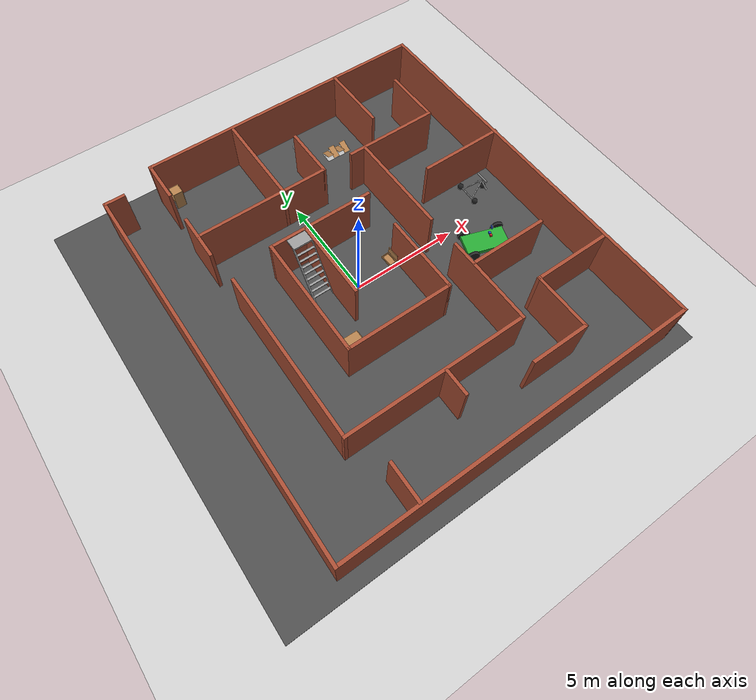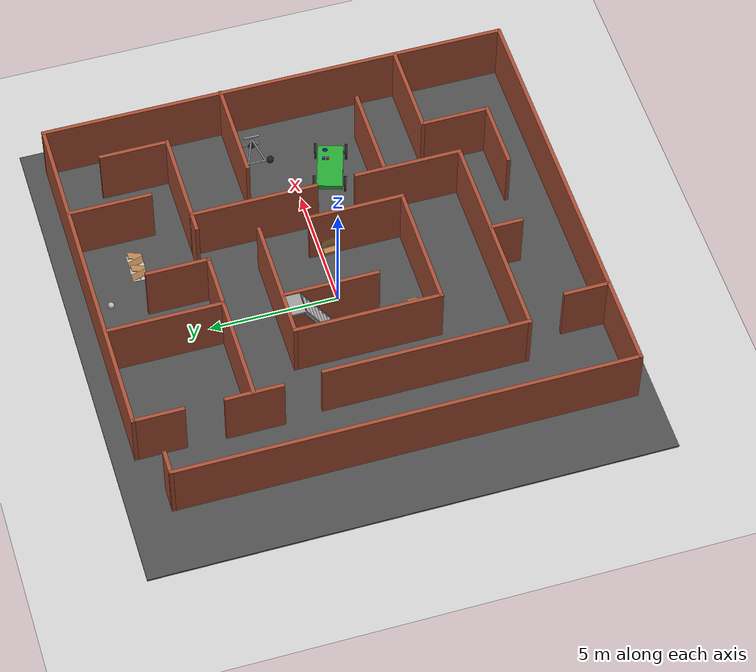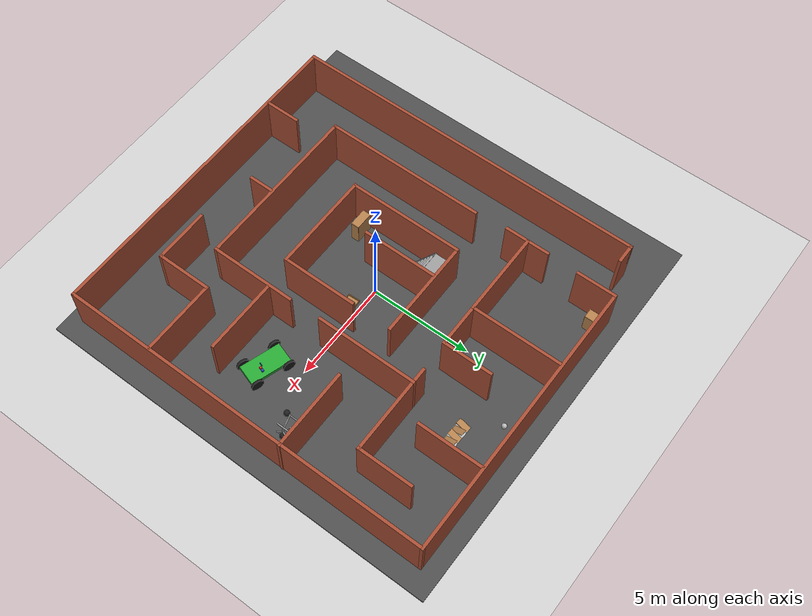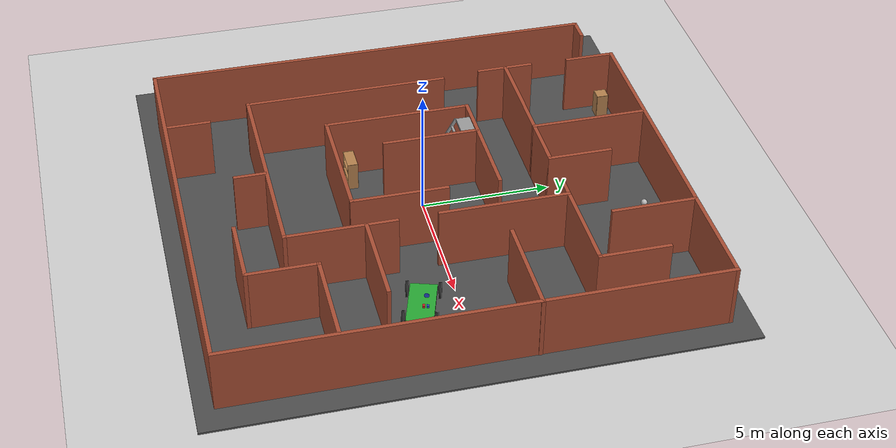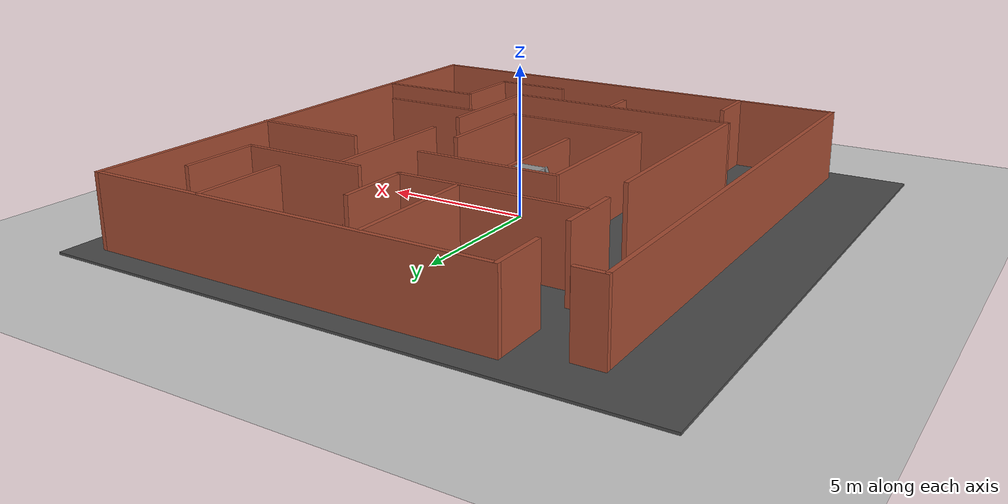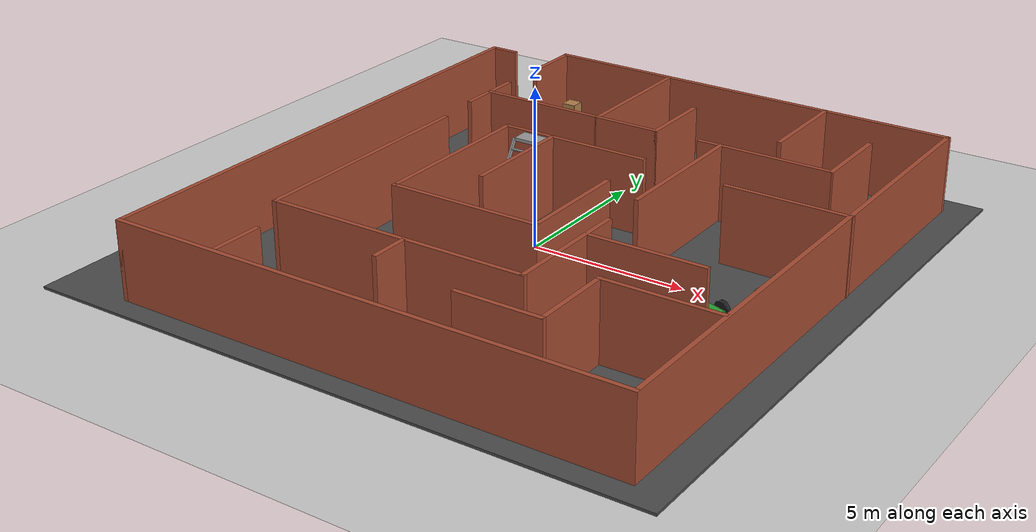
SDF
<sdf version="1.7">
 <world name="default">
  <light name="sun" type="directional">
   <pose>0 0 10 0 -0 0</pose>
   <diffuse>0.8 0.8 0.8 1</diffuse>
   <specular>0.2 0.2 0.2 1</specular>
   <attenuation>
    <range>1000</range>
    <constant>0.9</constant>
    <linear>0.01</linear>
    <quadratic>0.001</quadratic>
   </attenuation>
   <direction>-0.5 0.1 -0.9</direction>
   <spot><inner_angle>0</inner_angle><outer_angle>0</outer_angle><falloff>0</falloff></spot>
  </light>
  <model name="ground_plane">
   <static>1</static>
   <link name="link">
    <collision name="collision">
     <geometry><plane><normal>0 0 1</normal><size>100 100</size></plane></geometry>
     <surface>
      <contact><collide_bitmask>65535</collide_bitmask></contact>
      <friction><ode><mu>100</mu><mu2>50</mu2></ode></friction>
     </surface>
    </collision>
    <visual name="visual">
     <cast_shadows>0</cast_shadows>
     <geometry><plane><normal>0 0 1</normal><size>100 100</size></plane></geometry>
     <material>
      <script><uri>file://media/materials/scripts/gazebo.material</uri><name>Gazebo/Grey</name></script>
     </material>
    </visual>
   </link>
  </model>
  <gravity>0 0 -9.8</gravity>
  <magnetic_field>6e-06 2.3e-05 -4.2e-05</magnetic_field>
  <atmosphere type="adiabatic"/>
  <physics type="ode">
   <max_step_size>0.001</max_step_size>
   <real_time_factor>1</real_time_factor>
   <real_time_update_rate>1000</real_time_update_rate>
  </physics>
  <scene><ambient>0.4 0.4 0.4 1</ambient><background>0.7 0.7 0.7 1</background><shadows>1</shadows></scene>
  <spherical_coordinates>
   <surface_model>EARTH_WGS84</surface_model>
   <latitude_deg>0</latitude_deg>
   <longitude_deg>0</longitude_deg>
   <elevation>0</elevation>
   <heading_deg>0</heading_deg>
  </spherical_coordinates>
  <model name="walls">
   <pose>0.822707 -0.094534 0 0 -0 0</pose>
   <link name="Wall_10">
    <collision name="Wall_10_Collision">
     <geometry><box><size>2 0.15 2.5</size></box></geometry>
     <pose>0 0 1.25 0 -0 0</pose>
    </collision>
    <visual name="Wall_10_Visual">
     <pose>0 0 1.25 0 -0 0</pose>
     <geometry><box><size>2 0.15 2.5</size></box></geometry>
     <material>
      <script><uri>file://media/materials/scripts/gazebo.material</uri><name>Gazebo/Bricks</name></script>
      <ambient>1 1 1 1</ambient>
     </material>
     <meta><layer>0</layer></meta>
    </visual>
    <pose>-5.68821 8.25 0 0 -0 -1.5708</pose>
   </link>
   <link name="Wall_13">
    <collision name="Wall_13_Collision">
     <geometry><box><size>2.25 0.15 2.5</size></box></geometry>
     <pose>0 0 1.25 0 -0 0</pose>
    </collision>
    <visual name="Wall_13_Visual">
     <pose>0 0 1.25 0 -0 0</pose>
     <geometry><box><size>2.25 0.15 2.5</size></box></geometry>
     <material>
      <script><uri>file://media/materials/scripts/gazebo.material</uri><name>Gazebo/Bricks</name></script>
      <ambient>1 1 1 1</ambient>
     </material>
     <meta><layer>0</layer></meta>
    </visual>
    <pose>-5.72244 4.67661 0 0 -0 -1.5708</pose>
   </link>
   <link name="Wall_15">
    <collision name="Wall_15_Collision">
     <geometry><box><size>4.25 0.15 2.5</size></box></geometry>
     <pose>0 0 1.25 0 -0 0</pose>
    </collision>
    <visual name="Wall_15_Visual">
     <pose>0 0 1.25 0 -0 0</pose>
     <geometry><box><size>4.25 0.15 2.5</size></box></geometry>
     <material>
      <script><uri>file://media/materials/scripts/gazebo.material</uri><name>Gazebo/Bricks</name></script>
      <ambient>1 1 1 1</ambient>
     </material>
     <meta><layer>0</layer></meta>
    </visual>
    <pose>-3.62592 4.70309 0 0 -0 0</pose>
   </link>
   <link name="Wall_16">
    <collision name="Wall_16_Collision">
     <geometry><box><size>4.5 0.15 2.5</size></box></geometry>
     <pose>0 0 1.25 0 -0 0</pose>
    </collision>
    <visual name="Wall_16_Visual">
     <pose>0 0 1.25 0 -0 0</pose>
     <geometry><box><size>4.5 0.15 2.5</size></box></geometry>
     <material>
      <script><uri>file://media/materials/scripts/gazebo.material</uri><name>Gazebo/Bricks</name></script>
      <ambient>1 1 1 1</ambient>
     </material>
     <meta><layer>0</layer></meta>
    </visual>
    <pose>-1.57592 6.87809 0 0 -0 1.5708</pose>
   </link>
   <link name="Wall_18">
    <collision name="Wall_18_Collision">
     <geometry><box><size>2.25 0.15 2.5</size></box></geometry>
     <pose>0 0 1.25 0 -0 0</pose>
    </collision>
    <visual name="Wall_18_Visual">
     <pose>0 0 1.25 0 -0 0</pose>
     <geometry><box><size>2.25 0.15 2.5</size></box></geometry>
     <material>
      <script><uri>file://media/materials/scripts/gazebo.material</uri><name>Gazebo/Bricks</name></script>
      <ambient>1 1 1 1</ambient>
     </material>
     <meta><layer>0</layer></meta>
    </visual>
    <pose>-0.525917 4.70309 0 0 -0 0</pose>
   </link>
   <link name="Wall_20">
    <collision name="Wall_20_Collision">
     <geometry><box><size>4.5 0.15 2.5</size></box></geometry>
     <pose>0 0 1.25 0 -0 0</pose>
    </collision>
    <visual name="Wall_20_Visual">
     <pose>0 0 1.25 0 -0 0</pose>
     <geometry><box><size>4.5 0.15 2.5</size></box></geometry>
     <material>
      <script><uri>file://media/materials/scripts/gazebo.material</uri><name>Gazebo/Bricks</name></script>
      <ambient>1 1 1 1</ambient>
     </material>
     <meta><layer>0</layer></meta>
    </visual>
    <pose>4.22205 4.74961 0 0 -0 0</pose>
   </link>
   <link name="Wall_22">
    <collision name="Wall_22_Collision">
     <geometry><box><size>3.25 0.15 2.5</size></box></geometry>
     <pose>0 0 1.25 0 -0 0</pose>
    </collision>
    <visual name="Wall_22_Visual">
     <pose>0 0 1.25 0 -0 0</pose>
     <geometry><box><size>3.25 0.15 2.5</size></box></geometry>
     <material>
      <script><uri>file://media/materials/scripts/gazebo.material</uri><name>Gazebo/Bricks</name></script>
      <ambient>1 1 1 1</ambient>
     </material>
     <meta><layer>0</layer></meta>
    </visual>
    <pose>4.0941 7.57286 0 0 -0 -1.5708</pose>
   </link>
   <link name="Wall_24">
    <collision name="Wall_24_Collision">
     <geometry><box><size>5 0.15 2.5</size></box></geometry>
     <pose>0 0 1.25 0 -0 0</pose>
    </collision>
    <visual name="Wall_24_Visual">
     <pose>0 0 1.25 0 -0 0</pose>
     <geometry><box><size>5 0.15 2.5</size></box></geometry>
     <material>
      <script><uri>file://media/materials/scripts/gazebo.material</uri><name>Gazebo/Bricks</name></script>
      <ambient>1 1 1 1</ambient>
     </material>
     <meta><layer>0</layer></meta>
    </visual>
    <pose>2.74491 2.32461 0 0 -0 -1.5708</pose>
   </link>
   <link name="Wall_26">
    <collision name="Wall_26_Collision">
     <geometry><box><size>4.25 0.15 2.5</size></box></geometry>
     <pose>0 0 1.25 0 -0 0</pose>
    </collision>
    <visual name="Wall_26_Visual">
     <pose>0 0 1.25 0 -0 0</pose>
     <geometry><box><size>4.25 0.15 2.5</size></box></geometry>
     <material>
      <script><uri>file://media/materials/scripts/gazebo.material</uri><name>Gazebo/Bricks</name></script>
      <ambient>1 1 1 1</ambient>
     </material>
     <meta><layer>0</layer></meta>
    </visual>
    <pose>2.79144 -3.76721 0 0 -0 -1.5708</pose>
   </link>
   <link name="Wall_27">
    <collision name="Wall_27_Collision">
     <geometry><box><size>8.5 0.15 2.5</size></box></geometry>
     <pose>0 0 1.25 0 -0 0</pose>
    </collision>
    <visual name="Wall_27_Visual">
     <pose>0 0 1.25 0 -0 0</pose>
     <geometry><box><size>8.5 0.15 2.5</size></box></geometry>
     <material>
      <script><uri>file://media/materials/scripts/gazebo.material</uri><name>Gazebo/Bricks</name></script>
      <ambient>1 1 1 1</ambient>
     </material>
     <meta><layer>0</layer></meta>
    </visual>
    <pose>-1.38356 -5.81721 0 0 -0 3.14159</pose>
   </link>
   <link name="Wall_28">
    <collision name="Wall_28_Collision">
     <geometry><box><size>8 0.15 2.5</size></box></geometry>
     <pose>0 0 1.25 0 -0 0</pose>
    </collision>
    <visual name="Wall_28_Visual">
     <pose>0 0 1.25 0 -0 0</pose>
     <geometry><box><size>8 0.15 2.5</size></box></geometry>
     <material>
      <script><uri>file://media/materials/scripts/gazebo.material</uri><name>Gazebo/Bricks</name></script>
      <ambient>1 1 1 1</ambient>
     </material>
     <meta><layer>0</layer></meta>
    </visual>
    <pose>-5.55856 -1.89221 0 0 -0 1.5708</pose>
   </link>
   <link name="Wall_30">
    <collision name="Wall_30_Collision">
     <geometry><box><size>1.25 0.15 2.5</size></box></geometry>
     <pose>0 0 1.25 0 -0 0</pose>
    </collision>
    <visual name="Wall_30_Visual">
     <pose>0 0 1.25 0 -0 0</pose>
     <geometry><box><size>1.25 0.15 2.5</size></box></geometry>
     <material>
      <script><uri>file://media/materials/scripts/gazebo.material</uri><name>Gazebo/Bricks</name></script>
      <ambient>1 1 1 1</ambient>
     </material>
     <meta><layer>0</layer></meta>
    </visual>
    <pose>-1.02353 -6.45437 0 0 -0 -1.5708</pose>
   </link>
   <link name="Wall_32">
    <collision name="Wall_32_Collision">
     <geometry><box><size>1.75 0.15 2.5</size></box></geometry>
     <pose>0 0 1.25 0 -0 0</pose>
    </collision>
    <visual name="Wall_32_Visual">
     <pose>0 0 1.25 0 -0 0</pose>
     <geometry><box><size>1.75 0.15 2.5</size></box></geometry>
     <material>
      <script><uri>file://media/materials/scripts/gazebo.material</uri><name>Gazebo/Bricks</name></script>
      <ambient>1 1 1 1</ambient>
     </material>
     <meta><layer>0</layer></meta>
    </visual>
    <pose>-4.74544 -8.28618 0 0 -0 -1.5708</pose>
   </link>
   <link name="Wall_34">
    <collision name="Wall_34_Collision">
     <geometry><box><size>3.75 0.15 2.5</size></box></geometry>
     <pose>0 0 1.25 0 -0 0</pose>
    </collision>
    <visual name="Wall_34_Visual">
     <pose>0 0 1.25 0 -0 0</pose>
     <geometry><box><size>3.75 0.15 2.5</size></box></geometry>
     <material>
      <script><uri>file://media/materials/scripts/gazebo.material</uri><name>Gazebo/Bricks</name></script>
      <ambient>1 1 1 1</ambient>
     </material>
     <meta><layer>0</layer></meta>
    </visual>
    <pose>4.63796 -2.83379 0 0 -0 0</pose>
   </link>
   <link name="Wall_36">
    <collision name="Wall_36_Collision">
     <geometry><box><size>4 0.15 2.5</size></box></geometry>
     <pose>0 0 1.25 0 -0 0</pose>
    </collision>
    <visual name="Wall_36_Visual">
     <pose>0 0 1.25 0 -0 0</pose>
     <geometry><box><size>4 0.15 2.5</size></box></geometry>
     <material>
      <script><uri>file://media/materials/scripts/gazebo.material</uri><name>Gazebo/Bricks</name></script>
      <ambient>1 1 1 1</ambient>
     </material>
     <meta><layer>0</layer></meta>
    </visual>
    <pose>6.26321 2.14427 0 0 -0 3.14159</pose>
   </link>
   <link name="Wall_38">
    <collision name="Wall_38_Collision">
     <geometry><box><size>5 0.15 2.5</size></box></geometry>
     <pose>0 0 1.25 0 -0 0</pose>
    </collision>
    <visual name="Wall_38_Visual">
     <pose>0 0 1.25 0 -0 0</pose>
     <geometry><box><size>5 0.15 2.5</size></box></geometry>
     <material>
      <script><uri>file://media/materials/scripts/gazebo.material</uri><name>Gazebo/Bricks</name></script>
      <ambient>1 1 1 1</ambient>
     </material>
     <meta><layer>0</layer></meta>
    </visual>
    <pose>-1.07581 2.51646 0 0 -0 3.14159</pose>
   </link>
   <link name="Wall_39">
    <collision name="Wall_39_Collision">
     <geometry><box><size>5.75 0.15 2.5</size></box></geometry>
     <pose>0 0 1.25 0 -0 0</pose>
    </collision>
    <visual name="Wall_39_Visual">
     <pose>0 0 1.25 0 -0 0</pose>
     <geometry><box><size>5.75 0.15 2.5</size></box></geometry>
     <material>
      <script><uri>file://media/materials/scripts/gazebo.material</uri><name>Gazebo/Bricks</name></script>
      <ambient>1 1 1 1</ambient>
     </material>
     <meta><layer>0</layer></meta>
    </visual>
    <pose>-3.50081 -0.283537 0 0 -0 -1.5708</pose>
   </link>
   <link name="Wall_40">
    <collision name="Wall_40_Collision">
     <geometry><box><size>5 0.15 2.5</size></box></geometry>
     <pose>0 0 1.25 0 -0 0</pose>
    </collision>
    <visual name="Wall_40_Visual">
     <pose>0 0 1.25 0 -0 0</pose>
     <geometry><box><size>5 0.15 2.5</size></box></geometry>
     <material>
      <script><uri>file://media/materials/scripts/gazebo.material</uri><name>Gazebo/Bricks</name></script>
      <ambient>1 1 1 1</ambient>
     </material>
     <meta><layer>0</layer></meta>
    </visual>
    <pose>-1.07581 -3.08354 0 0 -0 0</pose>
   </link>
   <link name="Wall_41">
    <collision name="Wall_41_Collision">
     <geometry><box><size>3.75 0.15 2.5</size></box></geometry>
     <pose>0 0 1.25 0 -0 0</pose>
    </collision>
    <visual name="Wall_41_Visual">
     <pose>0 0 1.25 0 -0 0</pose>
     <geometry><box><size>3.75 0.15 2.5</size></box></geometry>
     <material>
      <script><uri>file://media/materials/scripts/gazebo.material</uri><name>Gazebo/Bricks</name></script>
      <ambient>1 1 1 1</ambient>
     </material>
     <meta><layer>0</layer></meta>
    </visual>
    <pose>1.34919 -1.28354 0 0 -0 1.5708</pose>
   </link>
   <link name="Wall_43">
    <collision name="Wall_43_Collision">
     <geometry><box><size>1 0.15 2.5</size></box></geometry>
     <pose>0 0 1.25 0 -0 0</pose>
    </collision>
    <visual name="Wall_43_Visual">
     <pose>0 0 1.25 0 -0 0</pose>
     <geometry><box><size>1 0.15 2.5</size></box></geometry>
     <material>
      <script><uri>file://media/materials/scripts/gazebo.material</uri><name>Gazebo/Bricks</name></script>
      <ambient>1 1 1 1</ambient>
     </material>
     <meta><layer>0</layer></meta>
    </visual>
    <pose>-7.76321 8.425 0 0 -0 0</pose>
   </link>
   <link name="Wall_46">
    <collision name="Wall_46_Collision">
     <geometry><box><size>2.5 0.15 2.5</size></box></geometry>
     <pose>0 0 1.25 0 -0 0</pose>
    </collision>
    <visual name="Wall_46_Visual">
     <pose>0 0 1.25 0 -0 0</pose>
     <geometry><box><size>2.5 0.15 2.5</size></box></geometry>
     <material>
      <script><uri>file://media/materials/scripts/gazebo.material</uri><name>Gazebo/Bricks</name></script>
      <ambient>1 1 1 1</ambient>
     </material>
     <meta><layer>0</layer></meta>
    </visual>
    <pose>0.524083 5.87809 0 0 -0 1.5708</pose>
   </link>
   <link name="Wall_48">
    <collision name="Wall_48_Collision">
     <geometry><box><size>2.75 0.15 2.5</size></box></geometry>
     <pose>0 0 1.25 0 -0 0</pose>
    </collision>
    <visual name="Wall_48_Visual">
     <pose>0 0 1.25 0 -0 0</pose>
     <geometry><box><size>2.75 0.15 2.5</size></box></geometry>
     <material>
      <script><uri>file://media/materials/scripts/gazebo.material</uri><name>Gazebo/Bricks</name></script>
      <ambient>1 1 1 1</ambient>
     </material>
     <meta><layer>0</layer></meta>
    </visual>
    <pose>6.39705 6.04961 0 0 -0 1.5708</pose>
   </link>
   <link name="Wall_5">
    <collision name="Wall_5_Collision">
     <geometry><box><size>17.75 0.15 2.5</size></box></geometry>
     <pose>0 0 1.25 0 -0 0</pose>
    </collision>
    <visual name="Wall_5_Visual">
     <pose>0 0 1.25 0 -0 0</pose>
     <geometry><box><size>17.75 0.15 2.5</size></box></geometry>
     <material>
      <script><uri>file://media/materials/scripts/gazebo.material</uri><name>Gazebo/Bricks</name></script>
      <ambient>1 1 1 1</ambient>
     </material>
     <meta><layer>0</layer></meta>
    </visual>
    <pose>-8.18821 -0.375 0 0 -0 -1.5708</pose>
   </link>
   <link name="Wall_50">
    <collision name="Wall_50_Collision">
     <geometry><box><size>3.75 0.15 2.5</size></box></geometry>
     <pose>0 0 1.25 0 -0 0</pose>
    </collision>
    <visual name="Wall_50_Visual">
     <pose>0 0 1.25 0 -0 0</pose>
     <geometry><box><size>3.75 0.15 2.5</size></box></geometry>
     <material>
      <script><uri>file://media/materials/scripts/gazebo.material</uri><name>Gazebo/Bricks</name></script>
      <ambient>1 1 1 1</ambient>
     </material>
     <meta><layer>0</layer></meta>
    </visual>
    <pose>6.29516 -4.88084 0 0 -0 3.14159</pose>
   </link>
   <link name="Wall_51">
    <collision name="Wall_51_Collision">
     <geometry><box><size>2.75 0.15 2.5</size></box></geometry>
     <pose>0 0 1.25 0 -0 0</pose>
    </collision>
    <visual name="Wall_51_Visual">
     <pose>0 0 1.25 0 -0 0</pose>
     <geometry><box><size>2.75 0.15 2.5</size></box></geometry>
     <material>
      <script><uri>file://media/materials/scripts/gazebo.material</uri><name>Gazebo/Bricks</name></script>
      <ambient>1 1 1 1</ambient>
     </material>
     <meta><layer>0</layer></meta>
    </visual>
    <pose>4.49516 -6.18084 0 0 -0 -1.5708</pose>
   </link>
   <link name="Wall_53">
    <collision name="Wall_53_Collision">
     <geometry><box><size>2.75 0.15 2.5</size></box></geometry>
     <pose>0 0 1.25 0 -0 0</pose>
    </collision>
    <visual name="Wall_53_Visual">
     <pose>0 0 1.25 0 -0 0</pose>
     <geometry><box><size>2.75 0.15 2.5</size></box></geometry>
     <material>
      <script><uri>file://media/materials/scripts/gazebo.material</uri><name>Gazebo/Bricks</name></script>
      <ambient>1 1 1 1</ambient>
     </material>
     <meta><layer>0</layer></meta>
    </visual>
    <pose>3.19516 -7.48084 0 0 -0 3.14159</pose>
   </link>
   <link name="Wall_55">
    <collision name="Wall_55_Collision">
     <geometry><box><size>3.75 0.15 2.5</size></box></geometry>
     <pose>0 0 1.25 0 -0 0</pose>
    </collision>
    <visual name="Wall_55_Visual">
     <pose>0 0 1.25 0 -0 0</pose>
     <geometry><box><size>3.75 0.15 2.5</size></box></geometry>
     <material>
      <script><uri>file://media/materials/scripts/gazebo.material</uri><name>Gazebo/Bricks</name></script>
      <ambient>1 1 1 1</ambient>
     </material>
     <meta><layer>0</layer></meta>
    </visual>
    <pose>-1.83759 0.657177 0 0 -0 -1.5708</pose>
   </link>
   <link name="Wall_6">
    <collision name="Wall_6_Collision">
     <geometry><box><size>16.5 0.15 2.5</size></box></geometry>
     <pose>0 0 1.25 0 -0 0</pose>
    </collision>
    <visual name="Wall_6_Visual">
     <pose>0 0 1.25 0 -0 0</pose>
     <geometry><box><size>16.5 0.15 2.5</size></box></geometry>
     <material>
      <script><uri>file://media/materials/scripts/gazebo.material</uri><name>Gazebo/Bricks</name></script>
      <ambient>1 1 1 1</ambient>
     </material>
     <meta><layer>0</layer></meta>
    </visual>
    <pose>-0.013208 -9.175 0 0 -0 0</pose>
   </link>
   <link name="Wall_7">
    <collision name="Wall_7_Collision">
     <geometry><box><size>18.5 0.15 2.5</size></box></geometry>
     <pose>0 0 1.25 0 -0 0</pose>
    </collision>
    <visual name="Wall_7_Visual">
     <pose>0 0 1.25 0 -0 0</pose>
     <geometry><box><size>18.5 0.15 2.5</size></box></geometry>
     <material>
      <script><uri>file://media/materials/scripts/gazebo.material</uri><name>Gazebo/Bricks</name></script>
      <ambient>1 1 1 1</ambient>
     </material>
     <meta><layer>0</layer></meta>
    </visual>
    <pose>8.16179 -0 0 0 -0 1.5708</pose>
   </link>
   <link name="Wall_8">
    <collision name="Wall_8_Collision">
     <geometry><box><size>14 0.15 2.5</size></box></geometry>
     <pose>0 0 1.25 0 -0 0</pose>
    </collision>
    <visual name="Wall_8_Visual">
     <pose>0 0 1.25 0 -0 0</pose>
     <geometry><box><size>14 0.15 2.5</size></box></geometry>
     <material>
      <script><uri>file://media/materials/scripts/gazebo.material</uri><name>Gazebo/Bricks</name></script>
      <ambient>1 1 1 1</ambient>
     </material>
     <meta><layer>0</layer></meta>
    </visual>
    <pose>1.23679 9.175 0 0 -0 3.14159</pose>
   </link>
   <static>1</static>
  </model>
  <model name="asphalt_plane">
   <static>1</static>
   <link name="link">
    <collision name="collision"><geometry><box><size>20 20 0.1</size></box></geometry></collision>
    <visual name="visual">
     <cast_shadows>0</cast_shadows>
     <geometry><box><size>20 20 0.1</size></box></geometry>
     <material>
      <script>
       <uri>model://asphalt_plane/materials/scripts</uri>
       <uri>model://asphalt_plane/materials/textures</uri>
       <name>vrc/asphalt</name>
      </script>
     </material>
    </visual>
   </link>
   <pose>0.038483 -0.02122 0 0 -0 0</pose>
  </model>
  <model name="trisphere_cycle">
   <link name="frame">
    <pose>-0.408559 0 0.385023 0 -0.522021 0</pose>
    <inertial>
     <mass>10</mass>
     <inertia><ixx>0.228</ixx><iyy>0.743521</iyy><izz>0.965521</izz><ixy>0</ixy><ixz>0</ixz><iyz>0</iyz></inertia>
    </inertial>
    <collision name="axle_collision">
     <pose>-0.471335 0 0 1.5708 -0 0</pose>
     <geometry><cylinder><length>1.03923</length><radius>0.03</radius></cylinder></geometry>
    </collision>
    <visual name="axle_visual">
     <pose>-0.471335 0 0 1.5708 -0 0</pose>
     <geometry><cylinder><length>1.03923</length><radius>0.03</radius></cylinder></geometry>
     <material>
      <script><uri>file://media/materials/scripts/gazebo.material</uri><name>Gazebo/Grey</name></script>
     </material>
    </visual>
    <collision name="frame_left_collision">
     <pose>0 0.171552 0 -2.79253 1.57079 3.14159</pose>
     <geometry><cylinder><length>1.00317</length><radius>0.03</radius></cylinder></geometry>
    </collision>
    <visual name="frame_left_visual">
     <pose>0 0.171552 0 -2.79253 1.57079 3.14159</pose>
     <geometry><cylinder><length>1.00317</length><radius>0.03</radius></cylinder></geometry>
     <material>
      <script><uri>file://media/materials/scripts/gazebo.material</uri><name>Gazebo/Grey</name></script>
     </material>
    </visual>
    <collision name="frame_right_collision">
     <pose>0 -0.171552 0 2.79253 1.57079 -3.14159</pose>
     <geometry><cylinder><length>1.00317</length><radius>0.03</radius></cylinder></geometry>
    </collision>
    <visual name="frame_right_visual">
     <pose>0 -0.171552 0 2.79253 1.57079 -3.14159</pose>
     <geometry><cylinder><length>1.00317</length><radius>0.03</radius></cylinder></geometry>
     <material>
      <script><uri>file://media/materials/scripts/gazebo.material</uri><name>Gazebo/Grey</name></script>
     </material>
    </visual>
   </link>
   <link name="fork">
    <pose>0.041441 0 0.385023 0 -0.174533 0</pose>
    <inertial>
     <mass>3</mass>
     <inertia>
      <ixx>0.158203</ixx>
      <iyy>0.0583594</iyy>
      <izz>0.102656</izz>
      <ixy>0</ixy>
      <ixz>0</ixz>
      <iyz>0</iyz>
     </inertia>
    </inertial>
    <collision name="handlebars_collision">
     <pose>0 0 0.397748 1.5708 -0 0</pose>
     <geometry><cylinder><length>0.636396</length><radius>0.0375</radius></cylinder></geometry>
    </collision>
    <visual name="handlebars_visual">
     <pose>0 0 0.397748 1.5708 -0 0</pose>
     <geometry><cylinder><length>0.636396</length><radius>0.0375</radius></cylinder></geometry>
     <material>
      <script><uri>file://media/materials/scripts/gazebo.material</uri><name>Gazebo/Grey</name></script>
     </material>
    </visual>
    <collision name="headtube_collision">
     <pose>0 0 0.238649 0 -0 0</pose>
     <geometry><cylinder><length>0.318198</length><radius>0.0375</radius></cylinder></geometry>
    </collision>
    <visual name="headtube_visual">
     <pose>0 0 0.238649 0 -0 0</pose>
     <geometry><cylinder><length>0.318198</length><radius>0.0375</radius></cylinder></geometry>
     <material>
      <script><uri>file://media/materials/scripts/gazebo.material</uri><name>Gazebo/Grey</name></script>
     </material>
    </visual>
    <collision name="spindle_collision">
     <pose>0 0 -0.238649 1.5708 -0 0</pose>
     <geometry><cylinder><length>0.636396</length><radius>0.015</radius></cylinder></geometry>
    </collision>
    <visual name="spindle_visual">
     <pose>0 0 -0.238649 1.5708 -0 0</pose>
     <geometry><cylinder><length>0.636396</length><radius>0.015</radius></cylinder></geometry>
     <material>
      <script><uri>file://media/materials/scripts/gazebo.material</uri><name>Gazebo/Grey</name></script>
     </material>
    </visual>
    <collision name="fork_left_collision">
     <pose>0 0.159099 -0.07955 0.785398 -0 0</pose>
     <geometry><cylinder><length>0.45</length><radius>0.0375</radius></cylinder></geometry>
    </collision>
    <visual name="fork_left_visual">
     <pose>0 0.159099 -0.07955 0.785398 -0 0</pose>
     <geometry><cylinder><length>0.45</length><radius>0.0375</radius></cylinder></geometry>
     <material>
      <script><uri>file://media/materials/scripts/gazebo.material</uri><name>Gazebo/Grey</name></script>
     </material>
    </visual>
    <collision name="fork_right_collision">
     <pose>0 -0.159099 -0.07955 -0.785398 0 0</pose>
     <geometry><cylinder><length>0.45</length><radius>0.0375</radius></cylinder></geometry>
    </collision>
    <visual name="fork_right_visual">
     <pose>0 -0.159099 -0.07955 -0.785398 0 0</pose>
     <geometry><cylinder><length>0.45</length><radius>0.0375</radius></cylinder></geometry>
     <material>
      <script><uri>file://media/materials/scripts/gazebo.material</uri><name>Gazebo/Grey</name></script>
     </material>
    </visual>
   </link>
   <link name="wheel_front">
    <pose>0.082882 0 0.15 0 -0 0</pose>
    <inertial>
     <mass>0.5</mass>
     <inertia><ixx>0.0045</ixx><iyy>0.0045</iyy><izz>0.0045</izz><ixy>0</ixy><ixz>0</ixz><iyz>0</iyz></inertia>
    </inertial>
    <collision name="collision">
     <geometry><sphere><radius>0.15</radius></sphere></geometry>
     <surface><contact><ode><kp>1e+08</kp><kd>1</kd><min_depth>0.0005</min_depth></ode></contact></surface>
    </collision>
    <visual name="visual">
     <geometry><sphere><radius>0.15</radius></sphere></geometry>
     <material>
      <script><uri>file://media/materials/scripts/gazebo.material</uri><name>Gazebo/Black</name></script>
     </material>
    </visual>
   </link>
   <joint name="wheel_front_steer" type="revolute">
    <parent>frame</parent>
    <child>fork</child>
    <axis>
     <xyz>0 0 1</xyz>
     <limit><lower>-0.959931</lower><upper>0.959931</upper></limit>
     <dynamics><spring_reference>0</spring_reference><spring_stiffness>0</spring_stiffness></dynamics>
    </axis>
   </joint>
   <joint name="wheel_front_spin" type="revolute">
    <parent>fork</parent>
    <child>wheel_front</child>
    <axis>
     <xyz>0 1 0</xyz>
     <limit><lower>-1e+16</lower><upper>1e+16</upper></limit>
     <dynamics><spring_reference>0</spring_reference><spring_stiffness>0</spring_stiffness></dynamics>
    </axis>
   </joint>
   <link name="wheel_rear_left">
    <pose>-0.817118 0.519615 0.15 0 -0 0</pose>
    <inertial>
     <mass>0.5</mass>
     <inertia><ixx>0.0045</ixx><iyy>0.0045</iyy><izz>0.0045</izz><ixy>0</ixy><ixz>0</ixz><iyz>0</iyz></inertia>
    </inertial>
    <collision name="collision">
     <geometry><sphere><radius>0.15</radius></sphere></geometry>
     <surface><contact><ode><kp>1e+08</kp><kd>1</kd><min_depth>0.0005</min_depth></ode></contact></surface>
    </collision>
    <visual name="visual">
     <geometry><sphere><radius>0.15</radius></sphere></geometry>
     <material>
      <script><uri>file://media/materials/scripts/gazebo.material</uri><name>Gazebo/Black</name></script>
     </material>
    </visual>
   </link>
   <joint name="wheel_rear_left_spin" type="revolute">
    <parent>frame</parent>
    <child>wheel_rear_left</child>
    <axis>
     <xyz>0 1 0</xyz>
     <limit><lower>-1e+16</lower><upper>1e+16</upper></limit>
     <dynamics><spring_reference>0</spring_reference><spring_stiffness>0</spring_stiffness></dynamics>
    </axis>
   </joint>
   <link name="wheel_rear_right">
    <pose>-0.817118 -0.519615 0.15 0 -0 0</pose>
    <inertial>
     <mass>0.5</mass>
     <inertia><ixx>0.0045</ixx><iyy>0.0045</iyy><izz>0.0045</izz><ixy>0</ixy><ixz>0</ixz><iyz>0</iyz></inertia>
    </inertial>
    <collision name="collision">
     <geometry><sphere><radius>0.15</radius></sphere></geometry>
     <surface><contact><ode><kp>1e+08</kp><kd>1</kd><min_depth>0.0005</min_depth></ode></contact></surface>
    </collision>
    <visual name="visual">
     <geometry><sphere><radius>0.15</radius></sphere></geometry>
     <material>
      <script><uri>file://media/materials/scripts/gazebo.material</uri><name>Gazebo/Black</name></script>
     </material>
    </visual>
   </link>
   <joint name="wheel_rear_right_spin" type="revolute">
    <parent>frame</parent>
    <child>wheel_rear_right</child>
    <axis>
     <xyz>0 1 0</xyz>
     <limit><lower>-1e+16</lower><upper>1e+16</upper></limit>
     <dynamics><spring_reference>0</spring_reference><spring_stiffness>0</spring_stiffness></dynamics>
    </axis>
   </joint>
   <pose>7.88283 1.17556 0.049499 0 1e-06 -0.007399</pose>
  </model>
  <model name="car">
   <link name="chassis">
    <pose>0 0 0.3 0 -0 0</pose>
    <collision name="collision"><geometry><box><size>2 1 0.2</size></box></geometry></collision>
    <visual name="visual">
     <geometry><box><size>2 1 0.2</size></box></geometry>
     <material>
      <script><uri>file://media/materials/scripts/gazebo.material</uri><name>Gazebo/Green</name></script>
     </material>
    </visual>
    <inertial>
     <inertia><ixx>1</ixx><ixy>0</ixy><ixz>0</ixz><iyy>1</iyy><iyz>0</iyz><izz>1</izz></inertia>
     <mass>1</mass>
    </inertial>
   </link>
   <link name="front_left_wheel">
    <pose>0.8 0.6 0.3 -0 1.5707 1.5707</pose>
    <collision name="collision">
     <geometry><cylinder><radius>0.3</radius><length>0.1</length></cylinder></geometry>
    </collision>
    <visual name="visual">
     <geometry><cylinder><radius>0.3</radius><length>0.1</length></cylinder></geometry>
     <material>
      <script><uri>file://media/materials/scripts/gazebo.material</uri><name>Gazebo/Black</name></script>
     </material>
    </visual>
    <inertial>
     <inertia><ixx>1</ixx><ixy>0</ixy><ixz>0</ixz><iyy>1</iyy><iyz>0</iyz><izz>1</izz></inertia>
     <mass>1</mass>
    </inertial>
   </link>
   <link name="front_right_wheel">
    <pose>0.8 -0.6 0.3 -0 1.5707 1.5707</pose>
    <collision name="collision">
     <geometry><cylinder><radius>0.3</radius><length>0.1</length></cylinder></geometry>
    </collision>
    <visual name="visual">
     <geometry><cylinder><radius>0.3</radius><length>0.1</length></cylinder></geometry>
     <material>
      <script><uri>file://media/materials/scripts/gazebo.material</uri><name>Gazebo/Black</name></script>
     </material>
    </visual>
    <inertial>
     <inertia><ixx>1</ixx><ixy>0</ixy><ixz>0</ixz><iyy>1</iyy><iyz>0</iyz><izz>1</izz></inertia>
     <mass>1</mass>
    </inertial>
   </link>
   <link name="back_right_wheel">
    <pose>-0.8 -0.6 0.3 -0 1.5707 1.5707</pose>
    <collision name="collision">
     <geometry><cylinder><radius>0.3</radius><length>0.1</length></cylinder></geometry>
    </collision>
    <visual name="visual">
     <geometry><cylinder><radius>0.3</radius><length>0.1</length></cylinder></geometry>
     <material>
      <script><uri>file://media/materials/scripts/gazebo.material</uri><name>Gazebo/Black</name></script>
     </material>
    </visual>
    <inertial>
     <inertia><ixx>1</ixx><ixy>0</ixy><ixz>0</ixz><iyy>1</iyy><iyz>0</iyz><izz>1</izz></inertia>
     <mass>1</mass>
    </inertial>
   </link>
   <link name="back_left_wheel">
    <pose>-0.8 0.6 0.3 -0 1.5707 1.5707</pose>
    <collision name="collision">
     <geometry><cylinder><radius>0.3</radius><length>0.1</length></cylinder></geometry>
    </collision>
    <visual name="visual">
     <geometry><cylinder><radius>0.3</radius><length>0.1</length></cylinder></geometry>
     <material>
      <script><uri>file://media/materials/scripts/gazebo.material</uri><name>Gazebo/Black</name></script>
     </material>
    </visual>
    <inertial>
     <inertia><ixx>1</ixx><ixy>0</ixy><ixz>0</ixz><iyy>1</iyy><iyz>0</iyz><izz>1</izz></inertia>
     <mass>1</mass>
    </inertial>
   </link>
   <link name="gas_pedal">
    <pose>0.3 0.1 0.5 0 -0 0</pose>
    <collision name="collision"><geometry><box><size>0.1 0.1 0.1</size></box></geometry></collision>
    <visual name="visual">
     <geometry><box><size>0.1 0.1 0.1</size></box></geometry>
     <material>
      <script><uri>file://media/materials/scripts/gazebo.material</uri><name>Gazebo/Red</name></script>
     </material>
    </visual>
    <inertial>
     <inertia><ixx>1</ixx><ixy>0</ixy><ixz>0</ixz><iyy>1</iyy><iyz>0</iyz><izz>1</izz></inertia>
     <mass>1</mass>
    </inertial>
   </link>
   <link name="brake_pedal">
    <pose>0.3 0.25 0.5 0 -0 0</pose>
    <collision name="collision"><geometry><box><size>0.1 0.1 0.1</size></box></geometry></collision>
    <visual name="visual">
     <geometry><box><size>0.1 0.1 0.1</size></box></geometry>
     <material>
      <script><uri>file://media/materials/scripts/gazebo.material</uri><name>Gazebo/Blue</name></script>
     </material>
    </visual>
    <inertial>
     <inertia><ixx>1</ixx><ixy>0</ixy><ixz>0</ixz><iyy>1</iyy><iyz>0</iyz><izz>1</izz></inertia>
     <mass>1</mass>
    </inertial>
   </link>
   <link name="steering_wheel">
    <pose>0.3 0.2 1 0 1.5707 0</pose>
    <collision name="collision">
     <geometry><cylinder><radius>0.1</radius><length>0.01</length></cylinder></geometry>
    </collision>
    <visual name="visual">
     <geometry><cylinder><radius>0.1</radius><length>0.01</length></cylinder></geometry>
     <material>
      <script><uri>file://media/materials/scripts/gazebo.material</uri><name>Gazebo/Blue</name></script>
     </material>
    </visual>
    <inertial>
     <inertia><ixx>1</ixx><ixy>0</ixy><ixz>0</ixz><iyy>1</iyy><iyz>0</iyz><izz>1</izz></inertia>
     <mass>1</mass>
    </inertial>
   </link>
   <joint name="gas_joint" type="prismatic">
    <parent>chassis</parent>
    <child>gas_pedal</child>
    <axis>
     <xyz expressed_in="__model__">1 0 0</xyz>
     <limit><lower>0</lower><upper>0.2</upper></limit>
     <dynamics><spring_reference>0</spring_reference><spring_stiffness>0</spring_stiffness></dynamics>
    </axis>
   </joint>
   <joint name="brake_joint" type="prismatic">
    <parent>chassis</parent>
    <child>brake_pedal</child>
    <axis>
     <xyz expressed_in="__model__">1 0 0</xyz>
     <limit><lower>0</lower><upper>0.2</upper></limit>
     <dynamics><spring_reference>0</spring_reference><spring_stiffness>0</spring_stiffness></dynamics>
    </axis>
   </joint>
   <joint name="steering_joint" type="revolute">
    <parent>chassis</parent>
    <child>steering_wheel</child>
    <axis>
     <xyz expressed_in="__model__">1 0 0</xyz>
     <limit><lower>-7.853</lower><upper>7.853</upper></limit>
     <dynamics><spring_reference>0</spring_reference><spring_stiffness>0</spring_stiffness></dynamics>
    </axis>
   </joint>
   <joint name="front_left_joint" type="revolute2">
    <parent>chassis</parent>
    <child>front_left_wheel</child>
    <axis>
     <xyz expressed_in="__model__">0 0 1</xyz>
     <limit><lower>0.00022976</lower><upper>0.00022976</upper></limit>
     <dynamics><spring_reference>0</spring_reference><spring_stiffness>0</spring_stiffness></dynamics>
    </axis>
    <axis2>
     <xyz expressed_in="__model__">0 1 0</xyz>
     <limit><upper>1e+16</upper><lower>-1e+16</lower></limit>
     <dynamics><spring_reference>0</spring_reference><spring_stiffness>0</spring_stiffness></dynamics>
    </axis2>
    <physics><ode><limit><cfm>0</cfm><erp>0.9</erp></limit></ode></physics>
   </joint>
   <joint name="front_right_joint" type="revolute2">
    <parent>chassis</parent>
    <child>front_right_wheel</child>
    <axis>
     <xyz expressed_in="__model__">0 0 1</xyz>
     <limit><lower>0.00022976</lower><upper>0.00022976</upper></limit>
     <dynamics><spring_reference>0</spring_reference><spring_stiffness>0</spring_stiffness></dynamics>
    </axis>
    <axis2>
     <xyz expressed_in="__model__">0 1 0</xyz>
     <limit><upper>1e+16</upper><lower>-1e+16</lower></limit>
     <dynamics><spring_reference>0</spring_reference><spring_stiffness>0</spring_stiffness></dynamics>
    </axis2>
    <physics><ode><limit><cfm>0</cfm><erp>0.9</erp></limit></ode></physics>
   </joint>
   <joint name="back_right_joint" type="revolute2">
    <parent>chassis</parent>
    <child>back_right_wheel</child>
    <axis>
     <xyz expressed_in="__model__">0 0 1</xyz>
     <limit><lower>0</lower><upper>0</upper></limit>
     <dynamics><spring_reference>0</spring_reference><spring_stiffness>0</spring_stiffness></dynamics>
    </axis>
    <axis2>
     <xyz expressed_in="__model__">0 1 0</xyz>
     <limit><upper>1e+16</upper><lower>-1e+16</lower></limit>
     <dynamics><spring_reference>0</spring_reference><spring_stiffness>0</spring_stiffness></dynamics>
    </axis2>
    <physics><ode><limit><cfm>0</cfm><erp>0.9</erp></limit></ode></physics>
   </joint>
   <joint name="back_left_joint" type="revolute2">
    <parent>chassis</parent>
    <child>back_left_wheel</child>
    <axis>
     <xyz expressed_in="__model__">0 0 1</xyz>
     <limit><lower>0</lower><upper>0</upper></limit>
     <dynamics><spring_reference>0</spring_reference><spring_stiffness>0</spring_stiffness></dynamics>
    </axis>
    <axis2>
     <xyz expressed_in="__model__">0 1 0</xyz>
     <limit><upper>1e+16</upper><lower>-1e+16</lower></limit>
     <dynamics><spring_reference>0</spring_reference><spring_stiffness>0</spring_stiffness></dynamics>
    </axis2>
    <physics><ode><limit><cfm>0</cfm><erp>0.9</erp></limit></ode></physics>
   </joint>
   <plugin name="vehicle" filename="libVehiclePlugin.so">
    <front_left>front_left_joint</front_left>
    <front_right>front_right_joint</front_right>
    <back_left>back_left_joint</back_left>
    <back_right>back_right_joint</back_right>
    <gas>gas_joint</gas>
    <brake>brake_joint</brake>
    <steering>steering_joint</steering>
    <front_power>10</front_power>
    <rear_power>10</rear_power>
    <tire_angle_range>0.5</tire_angle_range>
    <max_speed>10</max_speed>
    <aero_load>0.1</aero_load>
   </plugin>
   <pose>5.8996 -1.43866 0.050004 -2e-06 2e-06 -0.313952</pose>
  </model>
  <model name="wooden_case">
   <link name="base">
    <pose>0 0 0.024 0 -0 0</pose>
    <inertial>
     <pose>-0.022184 0 0.171592 0 -0 0</pose>
     <mass>3.96264</mass>
     <inertia>
      <ixx>0.213536</ixx>
      <ixy>0</ixy>
      <ixz>0.000779377</ixz>
      <iyy>0.0708943</iyy>
      <iyz>0</iyz>
      <izz>0.154604</izz>
     </inertia>
    </inertial>
    <collision name="collision_back">
     <pose>-0.053975 0 0.1778 0 -0 0</pose>
     <geometry><box><size>0.01905 0.5461 0.3175</size></box></geometry>
     <surface>
      <contact>
       <poissons_ratio>0.347</poissons_ratio>
       <elastic_modulus>8.8e+09</elastic_modulus>
       <ode><kp>100000</kp><kd>100</kd><max_vel>100</max_vel><min_depth>0.001</min_depth></ode>
      </contact>
      <friction>
       <torsional>
        <coefficient>1</coefficient>
        <use_patch_radius>0</use_patch_radius>
        <surface_radius>0.01</surface_radius>
       </torsional>
      </friction>
     </surface>
    </collision>
    <visual name="visual_back">
     <pose>-0.053975 0 0.1778 0 -0 0</pose>
     <geometry><box><size>0.01905 0.5461 0.3175</size></box></geometry>
     <material>
      <script><uri>file://media/materials/scripts/gazebo.material</uri><name>Gazebo/Wood</name></script>
     </material>
    </visual>
    <collision name="collision_bottom">
     <pose>0 0 0.009525 0 -0 0</pose>
     <geometry><box><size>0.127 0.5842 0.01905</size></box></geometry>
     <surface>
      <contact>
       <poissons_ratio>0.347</poissons_ratio>
       <elastic_modulus>8.8e+09</elastic_modulus>
       <ode><kp>100000</kp><kd>100</kd><max_vel>100</max_vel><min_depth>0.001</min_depth></ode>
      </contact>
      <friction>
       <torsional>
        <coefficient>1</coefficient>
        <use_patch_radius>0</use_patch_radius>
        <surface_radius>0.01</surface_radius>
       </torsional>
      </friction>
     </surface>
    </collision>
    <visual name="visual_bottom">
     <pose>0 0 0.009525 0 -0 0</pose>
     <geometry><box><size>0.127 0.5842 0.01905</size></box></geometry>
     <material>
      <script><uri>file://media/materials/scripts/gazebo.material</uri><name>Gazebo/Wood</name></script>
     </material>
    </visual>
    <collision name="collision_top">
     <pose>0 0 0.346075 0 -0 0</pose>
     <geometry><box><size>0.127 0.5842 0.01905</size></box></geometry>
     <surface>
      <contact>
       <poissons_ratio>0.347</poissons_ratio>
       <elastic_modulus>8.8e+09</elastic_modulus>
       <ode><kp>100000</kp><kd>100</kd><max_vel>100</max_vel><min_depth>0.001</min_depth></ode>
      </contact>
      <friction>
       <torsional>
        <coefficient>1</coefficient>
        <use_patch_radius>0</use_patch_radius>
        <surface_radius>0.01</surface_radius>
       </torsional>
      </friction>
     </surface>
    </collision>
    <visual name="visual_top">
     <pose>0 0 0.346075 0 -0 0</pose>
     <geometry><box><size>0.127 0.5842 0.01905</size></box></geometry>
     <material>
      <script><uri>file://media/materials/scripts/gazebo.material</uri><name>Gazebo/Wood</name></script>
     </material>
    </visual>
    <collision name="collision_left">
     <pose>0 -0.282575 0.1778 0 -0 0</pose>
     <geometry><box><size>0.127 0.01905 0.3175</size></box></geometry>
     <surface>
      <contact>
       <poissons_ratio>0.347</poissons_ratio>
       <elastic_modulus>8.8e+09</elastic_modulus>
       <ode><kp>100000</kp><kd>100</kd><max_vel>100</max_vel><min_depth>0.001</min_depth></ode>
      </contact>
      <friction>
       <torsional>
        <coefficient>1</coefficient>
        <use_patch_radius>0</use_patch_radius>
        <surface_radius>0.01</surface_radius>
       </torsional>
      </friction>
     </surface>
    </collision>
    <visual name="visual_left">
     <pose>0 -0.282575 0.1778 0 -0 0</pose>
     <geometry><box><size>0.127 0.01905 0.3175</size></box></geometry>
     <material>
      <script><uri>file://media/materials/scripts/gazebo.material</uri><name>Gazebo/Wood</name></script>
     </material>
    </visual>
    <collision name="collision_right">
     <pose>0 0.282575 0.1778 0 -0 0</pose>
     <geometry><box><size>0.127 0.01905 0.3175</size></box></geometry>
     <surface>
      <contact>
       <poissons_ratio>0.347</poissons_ratio>
       <elastic_modulus>8.8e+09</elastic_modulus>
       <ode><kp>100000</kp><kd>100</kd><max_vel>100</max_vel><min_depth>0.001</min_depth></ode>
      </contact>
      <friction>
       <torsional>
        <coefficient>1</coefficient>
        <use_patch_radius>0</use_patch_radius>
        <surface_radius>0.01</surface_radius>
       </torsional>
      </friction>
     </surface>
    </collision>
    <visual name="visual_right">
     <pose>0 0.282575 0.1778 0 -0 0</pose>
     <geometry><box><size>0.127 0.01905 0.3175</size></box></geometry>
     <material>
      <script><uri>file://media/materials/scripts/gazebo.material</uri><name>Gazebo/Wood</name></script>
     </material>
    </visual>
    <collision name="collision_block_left">
     <pose>0.0095 -0.2151 -0.012 0 -0 0</pose>
     <geometry><box><size>0.108 0.05 0.024</size></box></geometry>
     <surface>
      <contact>
       <poissons_ratio>0.347</poissons_ratio>
       <elastic_modulus>8.8e+09</elastic_modulus>
       <ode><kp>100000</kp><kd>100</kd><max_vel>100</max_vel><min_depth>0.001</min_depth></ode>
      </contact>
      <friction>
       <torsional>
        <coefficient>1</coefficient>
        <use_patch_radius>0</use_patch_radius>
        <surface_radius>0.01</surface_radius>
       </torsional>
      </friction>
     </surface>
    </collision>
    <visual name="visual_block_left">
     <pose>0.0095 -0.2151 -0.012 0 -0 0</pose>
     <geometry><box><size>0.108 0.05 0.024</size></box></geometry>
     <material>
      <script><uri>file://media/materials/scripts/gazebo.material</uri><name>Gazebo/Wood</name></script>
     </material>
    </visual>
    <collision name="collision_block_right">
     <pose>0.0095 0.2151 -0.012 0 -0 0</pose>
     <geometry><box><size>0.108 0.05 0.024</size></box></geometry>
     <surface>
      <contact>
       <poissons_ratio>0.347</poissons_ratio>
       <elastic_modulus>8.8e+09</elastic_modulus>
       <ode><kp>100000</kp><kd>100</kd><max_vel>100</max_vel><min_depth>0.001</min_depth></ode>
      </contact>
      <friction>
       <torsional>
        <coefficient>1</coefficient>
        <use_patch_radius>0</use_patch_radius>
        <surface_radius>0.01</surface_radius>
       </torsional>
      </friction>
     </surface>
    </collision>
    <visual name="visual_block_right">
     <pose>0.0095 0.2151 -0.012 0 -0 0</pose>
     <geometry><box><size>0.108 0.05 0.024</size></box></geometry>
     <material>
      <script><uri>file://media/materials/scripts/gazebo.material</uri><name>Gazebo/Wood</name></script>
     </material>
    </visual>
   </link>
   <link name="lid">
    <pose>0.243775 0 0.009525 0 -0 0</pose>
    <inertial>
     <mass>1.97874</mass>
     <inertia>
      <ixx>0.0563367</ixx>
      <ixy>0</ixy>
      <ixz>0</ixz>
      <iyy>0.020911</iyy>
      <iyz>0</iyz>
      <izz>0.0771281</izz>
     </inertia>
    </inertial>
    <collision name="collision">
     <geometry><box><size>0.3556 0.5842 0.01905</size></box></geometry>
     <surface>
      <contact>
       <poissons_ratio>0.347</poissons_ratio>
       <elastic_modulus>8.8e+09</elastic_modulus>
       <ode><kp>100000</kp><kd>100</kd><max_vel>100</max_vel><min_depth>0.001</min_depth></ode>
      </contact>
      <friction>
       <torsional>
        <coefficient>1</coefficient>
        <use_patch_radius>0</use_patch_radius>
        <surface_radius>0.01</surface_radius>
       </torsional>
      </friction>
     </surface>
    </collision>
    <visual name="visual">
     <geometry><box><size>0.3556 0.5842 0.01905</size></box></geometry>
     <material>
      <script><uri>file://media/materials/scripts/gazebo.material</uri><name>Gazebo/Wood</name></script>
     </material>
    </visual>
    <visual name="tee_nut_1">
     <pose>0.122 -0.216 0 0 -0 0</pose>
     <geometry><cylinder><radius>0.00635</radius><length>0.0192405</length></cylinder></geometry>
     <material>
      <script><uri>file://media/materials/scripts/gazebo.material</uri><name>Gazebo/Grey</name></script>
     </material>
    </visual>
    <visual name="tee_nut_2">
     <pose>0.122 -0.088 0 0 -0 0</pose>
     <geometry><cylinder><radius>0.00635</radius><length>0.0192405</length></cylinder></geometry>
     <material>
      <script><uri>file://media/materials/scripts/gazebo.material</uri><name>Gazebo/Grey</name></script>
     </material>
    </visual>
    <visual name="tee_nut_3">
     <pose>0.122 0.088 0 0 -0 0</pose>
     <geometry><cylinder><radius>0.00635</radius><length>0.0192405</length></cylinder></geometry>
     <material>
      <script><uri>file://media/materials/scripts/gazebo.material</uri><name>Gazebo/Grey</name></script>
     </material>
    </visual>
    <visual name="tee_nut_4">
     <pose>0.122 0.216 0 0 -0 0</pose>
     <geometry><cylinder><radius>0.00635</radius><length>0.0192405</length></cylinder></geometry>
     <material>
      <script><uri>file://media/materials/scripts/gazebo.material</uri><name>Gazebo/Grey</name></script>
     </material>
    </visual>
   </link>
   <joint name="lid_hinge" type="revolute">
    <pose>-0.1778 0 0.01905 0 -0 0</pose>
    <parent>base</parent>
    <child>lid</child>
    <axis>
     <xyz>0 1 0</xyz>
     <limit><upper>0.523599</upper><lower>-1.5708</lower></limit>
     <dynamics><spring_reference>0</spring_reference><spring_stiffness>0</spring_stiffness></dynamics>
    </axis>
   </joint>
   <pose>1.68966 -0.139565 1.11349 2.54351 -1.57075 -2.49713</pose>
  </model>
  <model name="cabinet">
   <static>1</static>
   <link name="cabinet_bottom_plate">
    <inertial>
     <pose>0 0 -1 0 -0 0</pose>
     <inertia><ixx>2.05</ixx><ixy>0</ixy><ixz>0</ixz><iyy>2.05</iyy><iyz>0</iyz><izz>2.05</izz></inertia>
     <mass>25</mass>
    </inertial>
    <collision name="cabinet_bottom_plate_geom">
     <pose>0 0 0.01 0 -0 0</pose>
     <geometry><box><size>0.45 0.45 0.02</size></box></geometry>
    </collision>
    <visual name="cabinet_bottom_plate_geom_visual">
     <pose>0 0 0.01 0 -0 0</pose>
     <geometry><box><size>0.45 0.45 0.02</size></box></geometry>
     <material>
      <script><uri>file://media/materials/scripts/gazebo.material</uri><name>Gazebo/Wood</name></script>
     </material>
    </visual>
    <collision name="cabinet_bottom_plate_geom_cabinet_back_plate">
     <pose>0.235 0 0.51 0 -0 0</pose>
     <geometry><box><size>0.02 0.45 1.02</size></box></geometry>
    </collision>
    <visual name="cabinet_bottom_plate_geom_cabinet_back_plate_visual">
     <pose>0.235 0 0.51 0 -0 0</pose>
     <geometry><box><size>0.02 0.45 1.02</size></box></geometry>
     <material>
      <script><uri>file://media/materials/scripts/gazebo.material</uri><name>Gazebo/Wood</name></script>
     </material>
    </visual>
    <collision name="cabinet_bottom_plate_geom_cabinet_left_plate">
     <pose>0 0.235 0.51 0 -0 0</pose>
     <geometry><box><size>0.45 0.02 1.02</size></box></geometry>
    </collision>
    <visual name="cabinet_bottom_plate_geom_cabinet_left_plate_visual">
     <pose>0 0.235 0.51 0 -0 0</pose>
     <geometry><box><size>0.45 0.02 1.02</size></box></geometry>
     <material>
      <script><uri>file://media/materials/scripts/gazebo.material</uri><name>Gazebo/Wood</name></script>
     </material>
    </visual>
    <collision name="cabinet_bottom_plate_geom_cabinet_middle_plate">
     <pose>0 0 0.51 0 -0 0</pose>
     <geometry><box><size>0.45 0.45 0.02</size></box></geometry>
    </collision>
    <visual name="cabinet_bottom_plate_geom_cabinet_middle_plate_visual">
     <pose>0 0 0.51 0 -0 0</pose>
     <geometry><box><size>0.45 0.45 0.02</size></box></geometry>
     <material>
      <script><uri>file://media/materials/scripts/gazebo.material</uri><name>Gazebo/Wood</name></script>
     </material>
    </visual>
    <collision name="cabinet_bottom_plate_geom_cabinet_right_plate">
     <pose>0 -0.235 0.51 0 -0 0</pose>
     <geometry><box><size>0.45 0.02 1.02</size></box></geometry>
    </collision>
    <visual name="cabinet_bottom_plate_geom_cabinet_right_plate_visual">
     <pose>0 -0.235 0.51 0 -0 0</pose>
     <geometry><box><size>0.45 0.02 1.02</size></box></geometry>
     <material>
      <script><uri>file://media/materials/scripts/gazebo.material</uri><name>Gazebo/Wood</name></script>
     </material>
    </visual>
    <collision name="cabinet_bottom_plate_geom_cabinet_top_plate">
     <pose>0 0 1.01 0 -0 0</pose>
     <geometry><box><size>0.45 0.45 0.02</size></box></geometry>
    </collision>
    <visual name="cabinet_bottom_plate_geom_cabinet_top_plate_visual">
     <pose>0 0 1.01 0 -0 0</pose>
     <geometry><box><size>0.45 0.45 0.02</size></box></geometry>
     <material>
      <script><uri>file://media/materials/scripts/gazebo.material</uri><name>Gazebo/Wood</name></script>
     </material>
    </visual>
   </link>
   <pose>-4.275 8.561 0 0 -0 0</pose>
  </model>
  <model name="bookshelf">
   <static>1</static>
   <link name="link">
    <inertial><mass>1</mass></inertial>
    <collision name="back">
     <pose>0 0.005 0.6 0 -0 0</pose>
     <geometry><box><size>0.9 0.01 1.2</size></box></geometry>
    </collision>
    <visual name="visual1">
     <pose>0 0.005 0.6 0 -0 0</pose>
     <geometry><box><size>0.9 0.01 1.2</size></box></geometry>
     <material>
      <script><uri>file://media/materials/scripts/gazebo.material</uri><name>Gazebo/Wood</name></script>
     </material>
    </visual>
    <collision name="left_side">
     <pose>0.45 -0.195 0.6 0 -0 0</pose>
     <geometry><box><size>0.02 0.4 1.2</size></box></geometry>
    </collision>
    <visual name="visual2">
     <pose>0.45 -0.195 0.6 0 -0 0</pose>
     <geometry><box><size>0.02 0.4 1.2</size></box></geometry>
     <material>
      <script><uri>file://media/materials/scripts/gazebo.material</uri><name>Gazebo/Wood</name></script>
     </material>
    </visual>
    <collision name="right_side">
     <pose>-0.45 -0.195 0.6 0 -0 0</pose>
     <geometry><box><size>0.02 0.4 1.2</size></box></geometry>
    </collision>
    <visual name="visual3">
     <pose>-0.45 -0.195 0.6 0 -0 0</pose>
     <geometry><box><size>0.02 0.4 1.2</size></box></geometry>
     <material>
      <script><uri>file://media/materials/scripts/gazebo.material</uri><name>Gazebo/Wood</name></script>
     </material>
    </visual>
    <collision name="bottom">
     <pose>0 -0.195 0.03 0 -0 0</pose>
     <geometry><box><size>0.88 0.4 0.06</size></box></geometry>
    </collision>
    <visual name="visual4">
     <pose>0 -0.195 0.03 0 -0 0</pose>
     <geometry><box><size>0.88 0.4 0.06</size></box></geometry>
     <material>
      <script><uri>file://media/materials/scripts/gazebo.material</uri><name>Gazebo/Wood</name></script>
     </material>
    </visual>
    <collision name="top">
     <pose>0 -0.195 1.19 0 -0 0</pose>
     <geometry><box><size>0.88 0.4 0.02</size></box></geometry>
    </collision>
    <visual name="visual5">
     <pose>0 -0.195 1.19 0 -0 0</pose>
     <geometry><box><size>0.88 0.4 0.02</size></box></geometry>
     <material>
      <script><uri>file://media/materials/scripts/gazebo.material</uri><name>Gazebo/Wood</name></script>
     </material>
    </visual>
    <collision name="low_shelf">
     <pose>0 -0.195 0.43 0 -0 0</pose>
     <geometry><box><size>0.88 0.4 0.02</size></box></geometry>
    </collision>
    <visual name="visual6">
     <pose>0 -0.195 0.43 0 -0 0</pose>
     <geometry><box><size>0.88 0.4 0.02</size></box></geometry>
     <material>
      <script><uri>file://media/materials/scripts/gazebo.material</uri><name>Gazebo/Wood</name></script>
     </material>
    </visual>
    <collision name="high_shelf">
     <pose>0 -0.195 0.8 0 -0 0</pose>
     <geometry><box><size>0.88 0.4 0.02</size></box></geometry>
    </collision>
    <visual name="visual7">
     <pose>0 -0.195 0.8 0 -0 0</pose>
     <geometry><box><size>0.88 0.4 0.02</size></box></geometry>
     <material>
      <script><uri>file://media/materials/scripts/gazebo.material</uri><name>Gazebo/Wood</name></script>
     </material>
    </visual>
   </link>
   <pose>-2.07172 -2.19696 0 0 -0 0</pose>
  </model>
  <model name="frc2016_ball">
   <pose>1.98746 8.30672 0.176984 0 -0 0</pose>
   <link name="link">
    <inertial>
     <mass>0.213</mass>
     <inertia>
      <ixx>0.00322667</ixx>
      <ixy>0</ixy>
      <ixz>0</ixz>
      <iyy>0.00322667</iyy>
      <iyz>0</iyz>
      <izz>0.00322667</izz>
     </inertia>
    </inertial>
    <visual name="visual"><geometry><sphere><radius>0.127</radius></sphere></geometry></visual>
    <collision name="collision">
     <geometry><sphere><radius>0.127</radius></sphere></geometry>
     <surface>
      <bounce><restitution_coefficient>0.15937</restitution_coefficient><threshold>0</threshold></bounce>
      <contact><ode><max_vel>100</max_vel><min_depth>0.001</min_depth></ode></contact>
     </surface>
    </collision>
   </link>
  </model>
  <model name="frc2016_chevaldefrise">
   <link name="base">
    <inertial>
     <mass>10</mass>
     <pose>0 0 0.15672 0 -0 0</pose>
     <inertia><ixx>0.380221</ixx><ixy>0</ixy><ixz>0</ixz><iyy>1.43365</iyy><iyz>0</iyz><izz>1.64745</izz></inertia>
    </inertial>
    <visual name="platform">
     <pose>0 0 0.06968 0 -0 0</pose>
     <geometry><box><size>1.27 0.5969 0.003175</size></box></geometry>
    </visual>
    <collision name="platform">
     <pose>0 0 0.06968 0 -0 0</pose>
     <geometry><box><size>1.27 0.5969 0.003175</size></box></geometry>
    </collision>
    <visual name="bar">
     <pose>0 0 0.16855 0 1.5707 0</pose>
     <geometry><cylinder><radius>0.02108</radius><length>1.273</length></cylinder></geometry>
    </visual>
    <collision name="bar">
     <pose>0 0 0.16855 0 1.5707 0</pose>
     <geometry><cylinder><radius>0.02108</radius><length>1.27</length></cylinder></geometry>
    </collision>
    <visual name="castor1">
     <pose>-0.45653 -0.16581 0.03175 0 -0 0</pose>
     <geometry><sphere><radius>0.03175</radius></sphere></geometry>
    </visual>
    <collision name="castor1">
     <pose>-0.45653 -0.16581 0.03175 0 -0 0</pose>
     <geometry><sphere><radius>0.03175</radius></sphere></geometry>
    </collision>
    <visual name="castor2">
     <pose>-0.27855 0.21408 0.03175 0 -0 0</pose>
     <geometry><sphere><radius>0.03175</radius></sphere></geometry>
    </visual>
    <collision name="castor2">
     <pose>-0.27855 0.21408 0.03175 0 -0 0</pose>
     <geometry><sphere><radius>0.03175</radius></sphere></geometry>
    </collision>
    <visual name="castor3">
     <pose>0.28191 0.21419 0.03175 0 -0 0</pose>
     <geometry><sphere><radius>0.03175</radius></sphere></geometry>
    </visual>
    <collision name="castor3">
     <pose>0.28191 0.21419 0.03175 0 -0 0</pose>
     <geometry><sphere><radius>0.03175</radius></sphere></geometry>
    </collision>
    <visual name="castor4">
     <pose>0.45965 -0.16602 0.03175 0 -0 0</pose>
     <geometry><sphere><radius>0.03175</radius></sphere></geometry>
    </visual>
    <collision name="castor4">
     <pose>0.45965 -0.16602 0.03175 0 -0 0</pose>
     <geometry><sphere><radius>0.03175</radius></sphere></geometry>
    </collision>
   </link>
   <link name="slant1">
    <pose>-0.4572 0.01307 0.1997 -0.39732 0 0</pose>
    <inertial>
     <pose>0 0.1 0 0 -0 0</pose>
     <mass>2</mass>
     <inertia>
      <ixx>0.0606857</ixx>
      <ixy>0</ixy>
      <ixz>0</ixz>
      <iyy>0.0148723</iyy>
      <iyz>0</iyz>
      <izz>0.0755042</izz>
     </inertia>
    </inertial>
    <visual name="visual">
     <geometry><box><size>0.29845 0.593285 0.0127</size></box></geometry>
     <material><script><name>Gazebo/WoodFloor</name><uri>__default__</uri></script></material>
    </visual>
    <collision name="collision"><geometry><box><size>0.29845 0.593285 0.0127</size></box></geometry></collision>
   </link>
   <link name="slant2">
    <pose>-0.1524 -0.01307 0.1997 0.39732 -0 0</pose>
    <inertial>
     <mass>2</mass>
     <pose>0 -0.1 0 0 -0 0</pose>
     <inertia>
      <ixx>0.0606857</ixx>
      <ixy>0</ixy>
      <ixz>0</ixz>
      <iyy>0.0148723</iyy>
      <iyz>0</iyz>
      <izz>0.0755042</izz>
     </inertia>
    </inertial>
    <visual name="visual">
     <geometry><box><size>0.29845 0.593285 0.0127</size></box></geometry>
     <material><script><name>Gazebo/WoodFloor</name><uri>__default__</uri></script></material>
    </visual>
    <collision name="collision"><geometry><box><size>0.29845 0.593285 0.0127</size></box></geometry></collision>
   </link>
   <link name="slant3">
    <pose>0.1524 0.01307 0.1997 -0.39732 0 0</pose>
    <inertial>
     <pose>0 0.1 0 0 -0 0</pose>
     <mass>2</mass>
     <inertia>
      <ixx>0.0606857</ixx>
      <ixy>0</ixy>
      <ixz>0</ixz>
      <iyy>0.0148723</iyy>
      <iyz>0</iyz>
      <izz>0.0755042</izz>
     </inertia>
    </inertial>
    <visual name="visual">
     <geometry><box><size>0.29845 0.593285 0.0127</size></box></geometry>
     <material><script><name>Gazebo/WoodFloor</name><uri>__default__</uri></script></material>
    </visual>
    <collision name="collision"><geometry><box><size>0.29845 0.593285 0.0127</size></box></geometry></collision>
   </link>
   <link name="slant4">
    <pose>0.4572 -0.01307 0.1997 0.39732 -0 0</pose>
    <inertial>
     <pose>0 -0.1 0 0 -0 0</pose>
     <mass>2</mass>
     <inertia>
      <ixx>0.0606857</ixx>
      <ixy>0</ixy>
      <ixz>0</ixz>
      <iyy>0.0148723</iyy>
      <iyz>0</iyz>
      <izz>0.0755042</izz>
     </inertia>
    </inertial>
    <visual name="visual">
     <geometry><box><size>0.29845 0.593285 0.0127</size></box></geometry>
     <material><script><name>Gazebo/WoodFloor</name><uri>__default__</uri></script></material>
    </visual>
    <collision name="collision"><geometry><box><size>0.29845 0.593285 0.0127</size></box></geometry></collision>
   </link>
   <joint name="slant1_joint" type="revolute">
    <parent>base</parent>
    <child>slant1</child>
    <axis>
     <xyz>1 0 0</xyz>
     <limit><lower>0</lower><upper>1.5707</upper></limit>
     <dynamics><spring_reference>0</spring_reference><spring_stiffness>0</spring_stiffness></dynamics>
    </axis>
   </joint>
   <joint name="slant2_joint" type="revolute">
    <parent>base</parent>
    <child>slant2</child>
    <axis>
     <xyz>1 0 0</xyz>
     <limit><lower>-1.5707</lower><upper>0</upper></limit>
     <dynamics><spring_reference>0</spring_reference><spring_stiffness>0</spring_stiffness></dynamics>
    </axis>
   </joint>
   <joint name="slant3_joint" type="revolute">
    <parent>base</parent>
    <child>slant3</child>
    <axis>
     <xyz>1 0 0</xyz>
     <limit><lower>0</lower><upper>1.5707</upper></limit>
     <dynamics><spring_reference>0</spring_reference><spring_stiffness>0</spring_stiffness></dynamics>
    </axis>
   </joint>
   <joint name="slant4_joint" type="revolute">
    <parent>base</parent>
    <child>slant4</child>
    <axis>
     <xyz>1 0 0</xyz>
     <limit><lower>-1.5707</lower><upper>0</upper></limit>
     <dynamics><spring_reference>0</spring_reference><spring_stiffness>0</spring_stiffness></dynamics>
    </axis>
   </joint>
   <pose>3.4856 6.91881 0.049996 -2.4e-05 -0 -0.028697</pose>
  </model>
  <model name="ladder_60deg_0rails">
   <static>1</static>
   <link name="step0">
    <pose>0 0.15396 0.266667 0 -0 0</pose>
    <inertial>
     <mass>9.75482</mass>
     <inertia>
      <ixx>0.00957124</ixx>
      <iyy>0.65963</iyy>
      <izz>0.666842</izz>
      <ixy>0</ixy>
      <ixz>0</ixz>
      <iyz>0</iyz>
     </inertia>
    </inertial>
    <collision name="collision"><geometry><box><size>0.9 0.1016 0.0381</size></box></geometry></collision>
    <visual name="visual">
     <geometry><box><size>0.9 0.1016 0.0381</size></box></geometry>
     <material>
      <script><uri>file://media/materials/scripts/gazebo.material</uri><name>Gazebo/Grey</name></script>
     </material>
    </visual>
   </link>
   <link name="step1">
    <pose>0 0.30792 0.533333 0 -0 0</pose>
    <inertial>
     <mass>9.75482</mass>
     <inertia>
      <ixx>0.00957124</ixx>
      <iyy>0.65963</iyy>
      <izz>0.666842</izz>
      <ixy>0</ixy>
      <ixz>0</ixz>
      <iyz>0</iyz>
     </inertia>
    </inertial>
    <collision name="collision"><geometry><box><size>0.9 0.1016 0.0381</size></box></geometry></collision>
    <visual name="visual">
     <geometry><box><size>0.9 0.1016 0.0381</size></box></geometry>
     <material>
      <script><uri>file://media/materials/scripts/gazebo.material</uri><name>Gazebo/Grey</name></script>
     </material>
    </visual>
   </link>
   <link name="step2">
    <pose>0 0.46188 0.8 0 -0 0</pose>
    <inertial>
     <mass>9.75482</mass>
     <inertia>
      <ixx>0.00957124</ixx>
      <iyy>0.65963</iyy>
      <izz>0.666842</izz>
      <ixy>0</ixy>
      <ixz>0</ixz>
      <iyz>0</iyz>
     </inertia>
    </inertial>
    <collision name="collision"><geometry><box><size>0.9 0.1016 0.0381</size></box></geometry></collision>
    <visual name="visual">
     <geometry><box><size>0.9 0.1016 0.0381</size></box></geometry>
     <material>
      <script><uri>file://media/materials/scripts/gazebo.material</uri><name>Gazebo/Grey</name></script>
     </material>
    </visual>
   </link>
   <link name="step3">
    <pose>0 0.61584 1.06667 0 -0 0</pose>
    <inertial>
     <mass>9.75482</mass>
     <inertia>
      <ixx>0.00957124</ixx>
      <iyy>0.65963</iyy>
      <izz>0.666842</izz>
      <ixy>0</ixy>
      <ixz>0</ixz>
      <iyz>0</iyz>
     </inertia>
    </inertial>
    <collision name="collision"><geometry><box><size>0.9 0.1016 0.0381</size></box></geometry></collision>
    <visual name="visual">
     <geometry><box><size>0.9 0.1016 0.0381</size></box></geometry>
     <material>
      <script><uri>file://media/materials/scripts/gazebo.material</uri><name>Gazebo/Grey</name></script>
     </material>
    </visual>
   </link>
   <link name="step4">
    <pose>0 0.7698 1.33333 0 -0 0</pose>
    <inertial>
     <mass>9.75482</mass>
     <inertia>
      <ixx>0.00957124</ixx>
      <iyy>0.65963</iyy>
      <izz>0.666842</izz>
      <ixy>0</ixy>
      <ixz>0</ixz>
      <iyz>0</iyz>
     </inertia>
    </inertial>
    <collision name="collision"><geometry><box><size>0.9 0.1016 0.0381</size></box></geometry></collision>
    <visual name="visual">
     <geometry><box><size>0.9 0.1016 0.0381</size></box></geometry>
     <material>
      <script><uri>file://media/materials/scripts/gazebo.material</uri><name>Gazebo/Grey</name></script>
     </material>
    </visual>
   </link>
   <link name="step5">
    <pose>0 0.92376 1.6 0 -0 0</pose>
    <inertial>
     <mass>9.75482</mass>
     <inertia>
      <ixx>0.00957124</ixx>
      <iyy>0.65963</iyy>
      <izz>0.666842</izz>
      <ixy>0</ixy>
      <ixz>0</ixz>
      <iyz>0</iyz>
     </inertia>
    </inertial>
    <collision name="collision"><geometry><box><size>0.9 0.1016 0.0381</size></box></geometry></collision>
    <visual name="visual">
     <geometry><box><size>0.9 0.1016 0.0381</size></box></geometry>
     <material>
      <script><uri>file://media/materials/scripts/gazebo.material</uri><name>Gazebo/Grey</name></script>
     </material>
    </visual>
   </link>
   <link name="step6">
    <pose>0 1.07772 1.86667 0 -0 0</pose>
    <inertial>
     <mass>9.75482</mass>
     <inertia>
      <ixx>0.00957124</ixx>
      <iyy>0.65963</iyy>
      <izz>0.666842</izz>
      <ixy>0</ixy>
      <ixz>0</ixz>
      <iyz>0</iyz>
     </inertia>
    </inertial>
    <collision name="collision"><geometry><box><size>0.9 0.1016 0.0381</size></box></geometry></collision>
    <visual name="visual">
     <geometry><box><size>0.9 0.1016 0.0381</size></box></geometry>
     <material>
      <script><uri>file://media/materials/scripts/gazebo.material</uri><name>Gazebo/Grey</name></script>
     </material>
    </visual>
   </link>
   <link name="step7">
    <pose>0 1.23168 2.13333 0 -0 0</pose>
    <inertial>
     <mass>9.75482</mass>
     <inertia>
      <ixx>0.00957124</ixx>
      <iyy>0.65963</iyy>
      <izz>0.666842</izz>
      <ixy>0</ixy>
      <ixz>0</ixz>
      <iyz>0</iyz>
     </inertia>
    </inertial>
    <collision name="collision"><geometry><box><size>0.9 0.1016 0.0381</size></box></geometry></collision>
    <visual name="visual">
     <geometry><box><size>0.9 0.1016 0.0381</size></box></geometry>
     <material>
      <script><uri>file://media/materials/scripts/gazebo.material</uri><name>Gazebo/Grey</name></script>
     </material>
    </visual>
   </link>
   <link name="landing">
    <pose>0 1.68564 2.4 0 -0 0</pose>
    <inertial>
     <mass>57.6072</mass>
     <inertia><ixx>1.73518</ixx><iyy>3.89545</iyy><izz>5.6167</izz><ixy>0</ixy><ixz>0</ixz><iyz>0</iyz></inertia>
    </inertial>
    <collision name="collision"><geometry><box><size>0.9 0.6 0.1016</size></box></geometry></collision>
    <visual name="visual">
     <geometry><box><size>0.9 0.6 0.1016</size></box></geometry>
     <material>
      <script><uri>file://media/materials/scripts/gazebo.material</uri><name>Gazebo/Grey</name></script>
     </material>
    </visual>
   </link>
   <link name="left_side_wall">
    <pose>-0.45 0.69282 1.2 1.0472 -0 0</pose>
    <collision name="collision"><geometry><box><size>0.0508 2.85128 0.13</size></box></geometry></collision>
    <visual name="visual">
     <geometry><box><size>0.0508 2.85128 0.13</size></box></geometry>
     <material>
      <script><uri>file://media/materials/scripts/gazebo.material</uri><name>Gazebo/Grey</name></script>
     </material>
    </visual>
   </link>
   <link name="right_side_wall">
    <pose>0.45 0.69282 1.2 1.0472 -0 0</pose>
    <collision name="collision"><geometry><box><size>0.0508 2.85128 0.13</size></box></geometry></collision>
    <visual name="visual">
     <geometry><box><size>0.0508 2.85128 0.13</size></box></geometry>
     <material>
      <script><uri>file://media/materials/scripts/gazebo.material</uri><name>Gazebo/Grey</name></script>
     </material>
    </visual>
   </link>
   <pose>-1.53148 0.408636 0 0 -0 0</pose>
  </model>
 </world>
</sdf>
